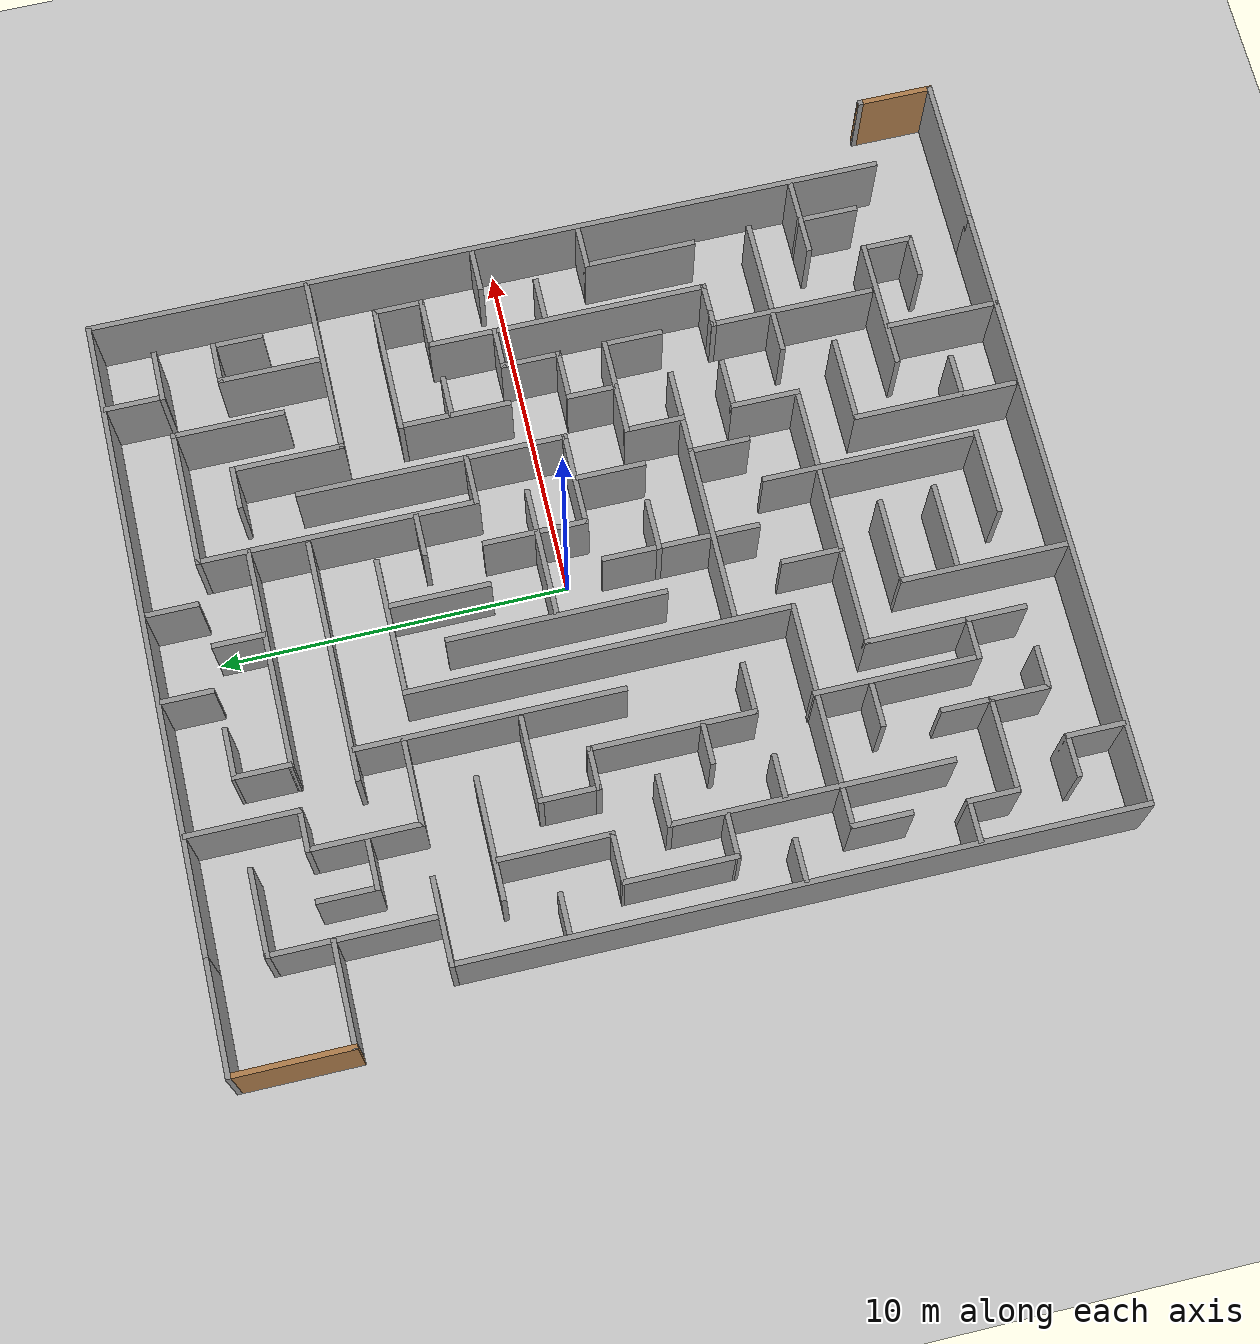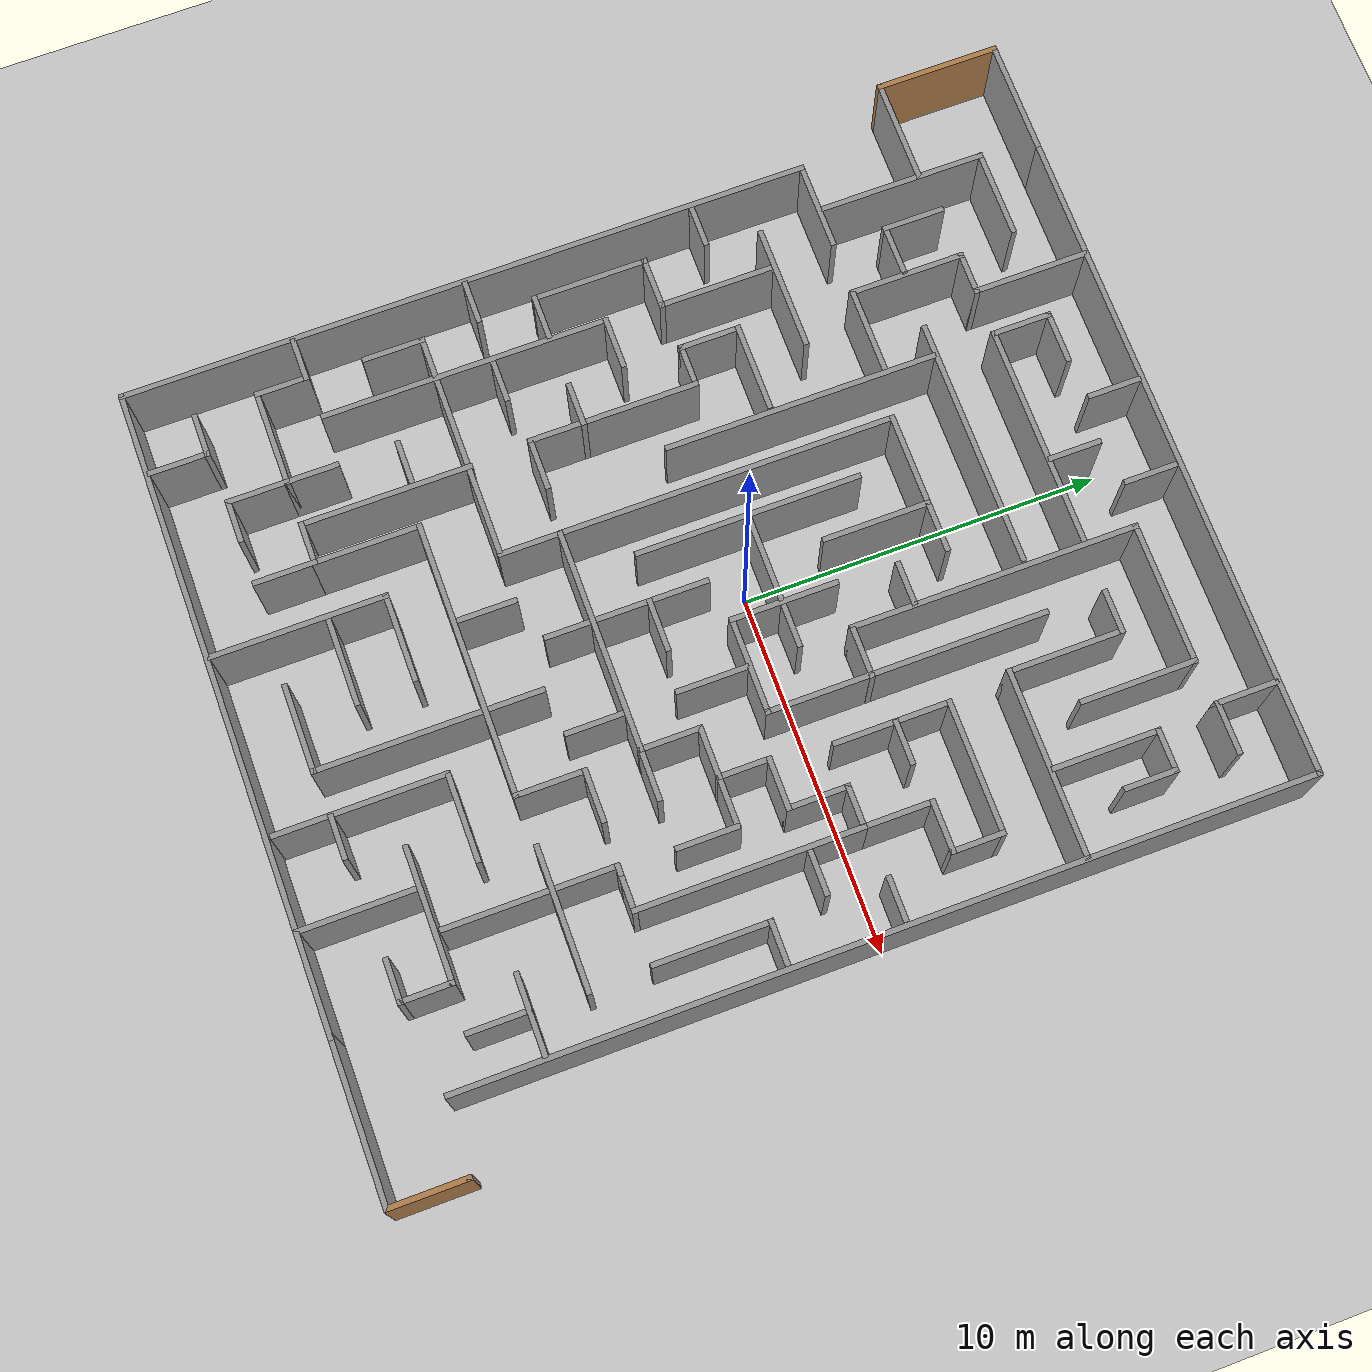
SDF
<sdf version="1.6">
 <world name="default">
  <plugin name="gazebo_occupancy_map" filename="libgazebo_grid_map_plugin.so">
   <map_resolution>0.05</map_resolution>
   <map_height>0.3</map_height>
   <map_size_x>30</map_size_x>
   <map_size_y>30</map_size_y>
   <init_robot_x>0</init_robot_x>
   <init_robot_y>0</init_robot_y>
  </plugin>
  <light name="sun" type="directional">
   <pose>0 0 10 0 -0 0</pose>
   <diffuse>0.8 0.8 0.8 1</diffuse>
   <specular>0.2 0.2 0.2 1</specular>
   <attenuation>
    <range>1000</range>
    <constant>0.9</constant>
    <linear>0.01</linear>
    <quadratic>0.001</quadratic>
   </attenuation>
   <direction>-0.5 0.1 -0.9</direction>
  </light>
  <model name="ground_plane">
   <static>1</static>
   <link name="link">
    <collision name="collision">
     <geometry><plane><normal>0 0 1</normal><size>100 100</size></plane></geometry>
     <surface><friction><ode><mu>100</mu><mu2>50</mu2></ode></friction></surface>
    </collision>
    <visual name="visual">
     <cast_shadows>0</cast_shadows>
     <geometry><plane><normal>0 0 1</normal><size>100 100</size></plane></geometry>
     <material>
      <script><uri>file://media/materials/scripts/gazebo.material</uri><name>Gazebo/Grey</name></script>
     </material>
    </visual>
   </link>
  </model>
  <gravity>0 0 -9.8</gravity>
  <magnetic_field>6e-06 2.3e-05 -4.2e-05</magnetic_field>
  <atmosphere type="adiabatic"/>
  <physics name="default_physics" default="0" type="ode">
   <max_step_size>0.001</max_step_size>
   <real_time_factor>1</real_time_factor>
   <real_time_update_rate>1000</real_time_update_rate>
  </physics>
  <scene><ambient>0.4 0.4 0.4 1</ambient><background>0.7 0.7 0.7 1</background><shadows>1</shadows></scene>
  <audio><device>default</device></audio>
  <spherical_coordinates>
   <surface_model>EARTH_WGS84</surface_model>
   <latitude_deg>0</latitude_deg>
   <longitude_deg>0</longitude_deg>
   <elevation>0</elevation>
   <heading_deg>0</heading_deg>
  </spherical_coordinates>
  <model name="maze">
   <pose>0.07616 -0.9851 0 0 -0 0</pose>
   <link name="Wall_10">
    <collision name="Wall_10_Collision">
     <geometry><box><size>18 0.15 2.5</size></box></geometry>
     <pose>0 0 1.25 0 -0 0</pose>
    </collision>
    <visual name="Wall_10_Visual">
     <pose>0 0 1.25 0 -0 0</pose>
     <geometry><box><size>18 0.15 2.5</size></box></geometry>
     <material>
      <script><uri>file://media/materials/scripts/gazebo.material</uri><name>Gazebo/Grey</name></script>
      <ambient>1 1 1 1</ambient>
     </material>
     <meta><layer>0</layer></meta>
    </visual>
    <pose>-1.40681 -12.6653 0 0 -0 0</pose>
   </link>
   <link name="Wall_100">
    <collision name="Wall_100_Collision">
     <geometry><box><size>1.5 0.15 2.5</size></box></geometry>
     <pose>0 0 1.25 0 -0 0</pose>
    </collision>
    <visual name="Wall_100_Visual">
     <pose>0 0 1.25 0 -0 0</pose>
     <geometry><box><size>1.5 0.15 2.5</size></box></geometry>
     <material>
      <script><uri>file://media/materials/scripts/gazebo.material</uri><name>Gazebo/Grey</name></script>
      <ambient>1 1 1 1</ambient>
     </material>
     <meta><layer>0</layer></meta>
    </visual>
    <pose>4.69711 -0.840511 0 0 -0 1.5708</pose>
   </link>
   <link name="Wall_101">
    <collision name="Wall_101_Collision">
     <geometry><box><size>1.5 0.15 2.5</size></box></geometry>
     <pose>0 0 1.25 0 -0 0</pose>
    </collision>
    <visual name="Wall_101_Visual">
     <pose>0 0 1.25 0 -0 0</pose>
     <geometry><box><size>1.5 0.15 2.5</size></box></geometry>
     <material>
      <script><uri>file://media/materials/scripts/gazebo.material</uri><name>Gazebo/Grey</name></script>
      <ambient>1 1 1 1</ambient>
     </material>
     <meta><layer>0</layer></meta>
    </visual>
    <pose>5.37211 -0.165511 0 0 -0 0</pose>
   </link>
   <link name="Wall_102">
    <collision name="Wall_102_Collision">
     <geometry><box><size>1.75 0.15 2.5</size></box></geometry>
     <pose>0 0 1.25 0 -0 0</pose>
    </collision>
    <visual name="Wall_102_Visual">
     <pose>0 0 1.25 0 -0 0</pose>
     <geometry><box><size>1.75 0.15 2.5</size></box></geometry>
     <material>
      <script><uri>file://media/materials/scripts/gazebo.material</uri><name>Gazebo/Grey</name></script>
      <ambient>1 1 1 1</ambient>
     </material>
     <meta><layer>0</layer></meta>
    </visual>
    <pose>6.04711 0.634489 0 0 -0 1.5708</pose>
   </link>
   <link name="Wall_103">
    <collision name="Wall_103_Collision">
     <geometry><box><size>1.25 0.15 2.5</size></box></geometry>
     <pose>0 0 1.25 0 -0 0</pose>
    </collision>
    <visual name="Wall_103_Visual">
     <pose>0 0 1.25 0 -0 0</pose>
     <geometry><box><size>1.25 0.15 2.5</size></box></geometry>
     <material>
      <script><uri>file://media/materials/scripts/gazebo.material</uri><name>Gazebo/Grey</name></script>
      <ambient>1 1 1 1</ambient>
     </material>
     <meta><layer>0</layer></meta>
    </visual>
    <pose>6.59711 1.43449 0 0 -0 0</pose>
   </link>
   <link name="Wall_104">
    <collision name="Wall_104_Collision">
     <geometry><box><size>6.25 0.15 2.5</size></box></geometry>
     <pose>0 0 1.25 0 -0 0</pose>
    </collision>
    <visual name="Wall_104_Visual">
     <pose>0 0 1.25 0 -0 0</pose>
     <geometry><box><size>6.25 0.15 2.5</size></box></geometry>
     <material>
      <script><uri>file://media/materials/scripts/gazebo.material</uri><name>Gazebo/Grey</name></script>
      <ambient>1 1 1 1</ambient>
     </material>
     <meta><layer>0</layer></meta>
    </visual>
    <pose>7.14711 -1.61551 0 0 -0 -1.5708</pose>
   </link>
   <link name="Wall_105">
    <collision name="Wall_105_Collision">
     <geometry><box><size>1 0.15 2.5</size></box></geometry>
     <pose>0 0 1.25 0 -0 0</pose>
    </collision>
    <visual name="Wall_105_Visual">
     <pose>0 0 1.25 0 -0 0</pose>
     <geometry><box><size>1 0.15 2.5</size></box></geometry>
     <material>
      <script><uri>file://media/materials/scripts/gazebo.material</uri><name>Gazebo/Grey</name></script>
      <ambient>1 1 1 1</ambient>
     </material>
     <meta><layer>0</layer></meta>
    </visual>
    <pose>6.72211 -4.66551 0 0 -0 3.14159</pose>
   </link>
   <link name="Wall_106">
    <collision name="Wall_106_Collision">
     <geometry><box><size>0.5 0.15 2.5</size></box></geometry>
     <pose>0 0 1.25 0 -0 0</pose>
    </collision>
    <visual name="Wall_106_Visual">
     <pose>0 0 1.25 0 -0 0</pose>
     <geometry><box><size>0.5 0.15 2.5</size></box></geometry>
     <material>
      <script><uri>file://media/materials/scripts/gazebo.material</uri><name>Gazebo/Grey</name></script>
      <ambient>1 1 1 1</ambient>
     </material>
     <meta><layer>0</layer></meta>
    </visual>
    <pose>6.12211 -4.66551 0 0 -0 3.14159</pose>
   </link>
   <link name="Wall_107">
    <collision name="Wall_107_Collision">
     <geometry><box><size>4.75 0.15 2.5</size></box></geometry>
     <pose>0 0 1.25 0 -0 0</pose>
    </collision>
    <visual name="Wall_107_Visual">
     <pose>0 0 1.25 0 -0 0</pose>
     <geometry><box><size>4.75 0.15 2.5</size></box></geometry>
     <material>
      <script><uri>file://media/materials/scripts/gazebo.material</uri><name>Gazebo/Grey</name></script>
      <ambient>1 1 1 1</ambient>
     </material>
     <meta><layer>0</layer></meta>
    </visual>
    <pose>5.94711 -6.96551 0 0 -0 -1.5708</pose>
   </link>
   <link name="Wall_109">
    <collision name="Wall_109_Collision">
     <geometry><box><size>4.5 0.15 2.5</size></box></geometry>
     <pose>0 0 1.25 0 -0 0</pose>
    </collision>
    <visual name="Wall_109_Visual">
     <pose>0 0 1.25 0 -0 0</pose>
     <geometry><box><size>4.5 0.15 2.5</size></box></geometry>
     <material>
      <script><uri>file://media/materials/scripts/gazebo.material</uri><name>Gazebo/Grey</name></script>
      <ambient>1 1 1 1</ambient>
     </material>
     <meta><layer>0</layer></meta>
    </visual>
    <pose>-0.252522 -2.20089 0 0 -0 -1.5708</pose>
   </link>
   <link name="Wall_111">
    <collision name="Wall_111_Collision">
     <geometry><box><size>1.5 0.15 2.5</size></box></geometry>
     <pose>0 0 1.25 0 -0 0</pose>
    </collision>
    <visual name="Wall_111_Visual">
     <pose>0 0 1.25 0 -0 0</pose>
     <geometry><box><size>1.5 0.15 2.5</size></box></geometry>
     <material>
      <script><uri>file://media/materials/scripts/gazebo.material</uri><name>Gazebo/Grey</name></script>
      <ambient>1 1 1 1</ambient>
     </material>
     <meta><layer>0</layer></meta>
    </visual>
    <pose>0.422478 -1.57708 0 0 -0 0</pose>
   </link>
   <link name="Wall_113">
    <collision name="Wall_113_Collision">
     <geometry><box><size>3 0.15 2.5</size></box></geometry>
     <pose>0 0 1.25 0 -0 0</pose>
    </collision>
    <visual name="Wall_113_Visual">
     <pose>0 0 1.25 0 -0 0</pose>
     <geometry><box><size>3 0.15 2.5</size></box></geometry>
     <material>
      <script><uri>file://media/materials/scripts/gazebo.material</uri><name>Gazebo/Grey</name></script>
      <ambient>1 1 1 1</ambient>
     </material>
     <meta><layer>0</layer></meta>
    </visual>
    <pose>-0.252522 4.66298 0 0 -0 -1.5708</pose>
   </link>
   <link name="Wall_115">
    <collision name="Wall_115_Collision">
     <geometry><box><size>6.25 0.15 2.5</size></box></geometry>
     <pose>0 0 1.25 0 -0 0</pose>
    </collision>
    <visual name="Wall_115_Visual">
     <pose>0 0 1.25 0 -0 0</pose>
     <geometry><box><size>6.25 0.15 2.5</size></box></geometry>
     <material>
      <script><uri>file://media/materials/scripts/gazebo.material</uri><name>Gazebo/Grey</name></script>
      <ambient>1 1 1 1</ambient>
     </material>
     <meta><layer>0</layer></meta>
    </visual>
    <pose>-1.56507 1.61746 0 0 -0 -1.5708</pose>
   </link>
   <link name="Wall_117">
    <collision name="Wall_117_Collision">
     <geometry><box><size>3.75 0.15 2.5</size></box></geometry>
     <pose>0 0 1.25 0 -0 0</pose>
    </collision>
    <visual name="Wall_117_Visual">
     <pose>0 0 1.25 0 -0 0</pose>
     <geometry><box><size>3.75 0.15 2.5</size></box></geometry>
     <material>
      <script><uri>file://media/materials/scripts/gazebo.material</uri><name>Gazebo/Grey</name></script>
      <ambient>1 1 1 1</ambient>
     </material>
     <meta><layer>0</layer></meta>
    </visual>
    <pose>0.354254 1.60485 0 0 -0 0</pose>
   </link>
   <link name="Wall_119">
    <collision name="Wall_119_Collision">
     <geometry><box><size>3 0.15 2.5</size></box></geometry>
     <pose>0 0 1.25 0 -0 0</pose>
    </collision>
    <visual name="Wall_119_Visual">
     <pose>0 0 1.25 0 -0 0</pose>
     <geometry><box><size>3 0.15 2.5</size></box></geometry>
     <material>
      <script><uri>file://media/materials/scripts/gazebo.material</uri><name>Gazebo/Grey</name></script>
      <ambient>1 1 1 1</ambient>
     </material>
     <meta><layer>0</layer></meta>
    </visual>
    <pose>0.940702 1.6515 0 0 -0 -1.5708</pose>
   </link>
   <link name="Wall_120">
    <collision name="Wall_120_Collision">
     <geometry><box><size>2.75 0.15 2.5</size></box></geometry>
     <pose>0 0 1.25 0 -0 0</pose>
    </collision>
    <visual name="Wall_120_Visual">
     <pose>0 0 1.25 0 -0 0</pose>
     <geometry><box><size>2.75 0.15 2.5</size></box></geometry>
     <material>
      <script><uri>file://media/materials/scripts/gazebo.material</uri><name>Gazebo/Grey</name></script>
      <ambient>1 1 1 1</ambient>
     </material>
     <meta><layer>0</layer></meta>
    </visual>
    <pose>2.2407 0.226497 0 0 -0 0</pose>
   </link>
   <link name="Wall_122">
    <collision name="Wall_122_Collision">
     <geometry><box><size>7.75 0.15 2.5</size></box></geometry>
     <pose>0 0 1.25 0 -0 0</pose>
    </collision>
    <visual name="Wall_122_Visual">
     <pose>0 0 1.25 0 -0 0</pose>
     <geometry><box><size>7.75 0.15 2.5</size></box></geometry>
     <material>
      <script><uri>file://media/materials/scripts/gazebo.material</uri><name>Gazebo/Grey</name></script>
      <ambient>1 1 1 1</ambient>
     </material>
     <meta><layer>0</layer></meta>
    </visual>
    <pose>3.5407 4.0265 0 0 -0 1.5708</pose>
   </link>
   <link name="Wall_124">
    <collision name="Wall_124_Collision">
     <geometry><box><size>2 0.15 2.5</size></box></geometry>
     <pose>0 0 1.25 0 -0 0</pose>
    </collision>
    <visual name="Wall_124_Visual">
     <pose>0 0 1.25 0 -0 0</pose>
     <geometry><box><size>2 0.15 2.5</size></box></geometry>
     <material>
      <script><uri>file://media/materials/scripts/gazebo.material</uri><name>Gazebo/Grey</name></script>
      <ambient>1 1 1 1</ambient>
     </material>
     <meta><layer>0</layer></meta>
    </visual>
    <pose>2.25325 -0.791789 0 0 -0 -1.5708</pose>
   </link>
   <link name="Wall_129">
    <collision name="Wall_129_Collision">
     <geometry><box><size>4.75 0.15 2.5</size></box></geometry>
     <pose>0 0 1.25 0 -0 0</pose>
    </collision>
    <visual name="Wall_129_Visual">
     <pose>0 0 1.25 0 -0 0</pose>
     <geometry><box><size>4.75 0.15 2.5</size></box></geometry>
     <material>
      <script><uri>file://media/materials/scripts/gazebo.material</uri><name>Gazebo/Grey</name></script>
      <ambient>1 1 1 1</ambient>
     </material>
     <meta><layer>0</layer></meta>
    </visual>
    <pose>2.25325 -10.1752 0 0 -0 1.5708</pose>
   </link>
   <link name="Wall_13">
    <collision name="Wall_13_Collision">
     <geometry><box><size>3.25 0.15 2.5</size></box></geometry>
     <pose>0 0 1.25 0 -0 0</pose>
    </collision>
    <visual name="Wall_13_Visual">
     <pose>0 0 1.25 0 -0 0</pose>
     <geometry><box><size>3.25 0.15 2.5</size></box></geometry>
     <material>
      <script><uri>file://media/materials/scripts/gazebo.material</uri><name>Gazebo/Grey</name></script>
      <ambient>1 1 1 1</ambient>
     </material>
     <meta><layer>0</layer></meta>
    </visual>
    <pose>-5.35339 11.0598 0 0 -0 -1.5708</pose>
   </link>
   <link name="Wall_130">
    <collision name="Wall_130_Collision">
     <geometry><box><size>2.5 0.15 2.5</size></box></geometry>
     <pose>0 0 1.25 0 -0 0</pose>
    </collision>
    <visual name="Wall_130_Visual">
     <pose>0 0 1.25 0 -0 0</pose>
     <geometry><box><size>2.5 0.15 2.5</size></box></geometry>
     <material>
      <script><uri>file://media/materials/scripts/gazebo.material</uri><name>Gazebo/Grey</name></script>
      <ambient>1 1 1 1</ambient>
     </material>
     <meta><layer>0</layer></meta>
    </visual>
    <pose>3.42825 -7.87519 0 0 -0 0</pose>
   </link>
   <link name="Wall_132">
    <collision name="Wall_132_Collision">
     <geometry><box><size>1.25 0.15 2.5</size></box></geometry>
     <pose>0 0 1.25 0 -0 0</pose>
    </collision>
    <visual name="Wall_132_Visual">
     <pose>0 0 1.25 0 -0 0</pose>
     <geometry><box><size>1.25 0.15 2.5</size></box></geometry>
     <material>
      <script><uri>file://media/materials/scripts/gazebo.material</uri><name>Gazebo/Grey</name></script>
      <ambient>1 1 1 1</ambient>
     </material>
     <meta><layer>0</layer></meta>
    </visual>
    <pose>2.84302 -10.9638 0 0 -0 0</pose>
   </link>
   <link name="Wall_134">
    <collision name="Wall_134_Collision">
     <geometry><box><size>3.75 0.15 2.5</size></box></geometry>
     <pose>0 0 1.25 0 -0 0</pose>
    </collision>
    <visual name="Wall_134_Visual">
     <pose>0 0 1.25 0 -0 0</pose>
     <geometry><box><size>3.75 0.15 2.5</size></box></geometry>
     <material>
      <script><uri>file://media/materials/scripts/gazebo.material</uri><name>Gazebo/Grey</name></script>
      <ambient>1 1 1 1</ambient>
     </material>
     <meta><layer>0</layer></meta>
    </visual>
    <pose>5.48512 -9.45236 0 0 -0 0</pose>
   </link>
   <link name="Wall_135">
    <collision name="Wall_135_Collision">
     <geometry><box><size>1.5 0.15 2.5</size></box></geometry>
     <pose>0 0 1.25 0 -0 0</pose>
    </collision>
    <visual name="Wall_135_Visual">
     <pose>0 0 1.25 0 -0 0</pose>
     <geometry><box><size>1.5 0.15 2.5</size></box></geometry>
     <material>
      <script><uri>file://media/materials/scripts/gazebo.material</uri><name>Gazebo/Grey</name></script>
      <ambient>1 1 1 1</ambient>
     </material>
     <meta><layer>0</layer></meta>
    </visual>
    <pose>7.28512 -10.1274 0 0 -0 -1.5708</pose>
   </link>
   <link name="Wall_136">
    <collision name="Wall_136_Collision">
     <geometry><box><size>1.25 0.15 2.5</size></box></geometry>
     <pose>0 0 1.25 0 -0 0</pose>
    </collision>
    <visual name="Wall_136_Visual">
     <pose>0 0 1.25 0 -0 0</pose>
     <geometry><box><size>1.25 0.15 2.5</size></box></geometry>
     <material>
      <script><uri>file://media/materials/scripts/gazebo.material</uri><name>Gazebo/Grey</name></script>
      <ambient>1 1 1 1</ambient>
     </material>
     <meta><layer>0</layer></meta>
    </visual>
    <pose>6.73512 -10.8024 0 0 -0 3.14159</pose>
   </link>
   <link name="Wall_138">
    <collision name="Wall_138_Collision">
     <geometry><box><size>3.25 0.15 2.5</size></box></geometry>
     <pose>0 0 1.25 0 -0 0</pose>
    </collision>
    <visual name="Wall_138_Visual">
     <pose>0 0 1.25 0 -0 0</pose>
     <geometry><box><size>3.25 0.15 2.5</size></box></geometry>
     <material>
      <script><uri>file://media/materials/scripts/gazebo.material</uri><name>Gazebo/Grey</name></script>
      <ambient>1 1 1 1</ambient>
     </material>
     <meta><layer>0</layer></meta>
    </visual>
    <pose>4.75902 -11.0819 0 0 -0 -1.5708</pose>
   </link>
   <link name="Wall_14">
    <collision name="Wall_14_Collision">
     <geometry><box><size>1.25 0.15 2.5</size></box></geometry>
     <pose>0 0 1.25 0 -0 0</pose>
    </collision>
    <visual name="Wall_14_Visual">
     <pose>0 0 1.25 0 -0 0</pose>
     <geometry><box><size>1.25 0.15 2.5</size></box></geometry>
     <material>
      <script><uri>file://media/materials/scripts/gazebo.material</uri><name>Gazebo/Grey</name></script>
      <ambient>1 1 1 1</ambient>
     </material>
     <meta><layer>0</layer></meta>
    </visual>
    <pose>-5.90339 9.5098 0 0 -0 3.14159</pose>
   </link>
   <link name="Wall_140">
    <collision name="Wall_140_Collision">
     <geometry><box><size>2.25 0.15 2.5</size></box></geometry>
     <pose>0 0 1.25 0 -0 0</pose>
    </collision>
    <visual name="Wall_140_Visual">
     <pose>0 0 1.25 0 -0 0</pose>
     <geometry><box><size>2.25 0.15 2.5</size></box></geometry>
     <material>
      <script><uri>file://media/materials/scripts/gazebo.material</uri><name>Gazebo/Grey</name></script>
      <ambient>1 1 1 1</ambient>
     </material>
     <meta><layer>0</layer></meta>
    </visual>
    <pose>8.68079 -7.90117 0 0 -0 3.14159</pose>
   </link>
   <link name="Wall_142">
    <collision name="Wall_142_Collision">
     <geometry><box><size>1.75 0.15 2.5</size></box></geometry>
     <pose>0 0 1.25 0 -0 0</pose>
    </collision>
    <visual name="Wall_142_Visual">
     <pose>0 0 1.25 0 -0 0</pose>
     <geometry><box><size>1.75 0.15 2.5</size></box></geometry>
     <material>
      <script><uri>file://media/materials/scripts/gazebo.material</uri><name>Gazebo/Grey</name></script>
      <ambient>1 1 1 1</ambient>
     </material>
     <meta><layer>0</layer></meta>
    </visual>
    <pose>8.57734 -8.70116 0 0 -0 -1.5708</pose>
   </link>
   <link name="Wall_144">
    <collision name="Wall_144_Collision">
     <geometry><box><size>4 0.15 2.5</size></box></geometry>
     <pose>0 0 1.25 0 -0 0</pose>
    </collision>
    <visual name="Wall_144_Visual">
     <pose>0 0 1.25 0 -0 0</pose>
     <geometry><box><size>4 0.15 2.5</size></box></geometry>
     <material>
      <script><uri>file://media/materials/scripts/gazebo.material</uri><name>Gazebo/Grey</name></script>
      <ambient>1 1 1 1</ambient>
     </material>
     <meta><layer>0</layer></meta>
    </visual>
    <pose>6.72379 -6.38975 0 0 -0 0</pose>
   </link>
   <link name="Wall_146">
    <collision name="Wall_146_Collision">
     <geometry><box><size>3.25 0.15 2.5</size></box></geometry>
     <pose>0 0 1.25 0 -0 0</pose>
    </collision>
    <visual name="Wall_146_Visual">
     <pose>0 0 1.25 0 -0 0</pose>
     <geometry><box><size>3.25 0.15 2.5</size></box></geometry>
     <material>
      <script><uri>file://media/materials/scripts/gazebo.material</uri><name>Gazebo/Grey</name></script>
      <ambient>1 1 1 1</ambient>
     </material>
     <meta><layer>0</layer></meta>
    </visual>
    <pose>8.57734 -3.12946 0 0 -0 1.5708</pose>
   </link>
   <link name="Wall_147">
    <collision name="Wall_147_Collision">
     <geometry><box><size>1.25 0.15 2.5</size></box></geometry>
     <pose>0 0 1.25 0 -0 0</pose>
    </collision>
    <visual name="Wall_147_Visual">
     <pose>0 0 1.25 0 -0 0</pose>
     <geometry><box><size>1.25 0.15 2.5</size></box></geometry>
     <material>
      <script><uri>file://media/materials/scripts/gazebo.material</uri><name>Gazebo/Grey</name></script>
      <ambient>1 1 1 1</ambient>
     </material>
     <meta><layer>0</layer></meta>
    </visual>
    <pose>9.12734 -1.57946 0 0 -0 0</pose>
   </link>
   <link name="Wall_149">
    <collision name="Wall_149_Collision">
     <geometry><box><size>2 0.15 2.5</size></box></geometry>
     <pose>0 0 1.25 0 -0 0</pose>
    </collision>
    <visual name="Wall_149_Visual">
     <pose>0 0 1.25 0 -0 0</pose>
     <geometry><box><size>2 0.15 2.5</size></box></geometry>
     <material>
      <script><uri>file://media/materials/scripts/gazebo.material</uri><name>Gazebo/Grey</name></script>
      <ambient>1 1 1 1</ambient>
     </material>
     <meta><layer>0</layer></meta>
    </visual>
    <pose>7.14711 2.35949 0 0 -0 1.5708</pose>
   </link>
   <link name="Wall_15">
    <collision name="Wall_15_Collision">
     <geometry><box><size>3.25 0.15 2.5</size></box></geometry>
     <pose>0 0 1.25 0 -0 0</pose>
    </collision>
    <visual name="Wall_15_Visual">
     <pose>0 0 1.25 0 -0 0</pose>
     <geometry><box><size>3.25 0.15 2.5</size></box></geometry>
     <material>
      <script><uri>file://media/materials/scripts/gazebo.material</uri><name>Gazebo/Grey</name></script>
      <ambient>1 1 1 1</ambient>
     </material>
     <meta><layer>0</layer></meta>
    </visual>
    <pose>-6.45339 7.9598 0 0 -0 -1.5708</pose>
   </link>
   <link name="Wall_150">
    <collision name="Wall_150_Collision">
     <geometry><box><size>1.5 0.15 2.5</size></box></geometry>
     <pose>0 0 1.25 0 -0 0</pose>
    </collision>
    <visual name="Wall_150_Visual">
     <pose>0 0 1.25 0 -0 0</pose>
     <geometry><box><size>1.5 0.15 2.5</size></box></geometry>
     <material>
      <script><uri>file://media/materials/scripts/gazebo.material</uri><name>Gazebo/Grey</name></script>
      <ambient>1 1 1 1</ambient>
     </material>
     <meta><layer>0</layer></meta>
    </visual>
    <pose>7.82211 3.28449 0 0 -0 0</pose>
   </link>
   <link name="Wall_151">
    <collision name="Wall_151_Collision">
     <geometry><box><size>1.5 0.15 2.5</size></box></geometry>
     <pose>0 0 1.25 0 -0 0</pose>
    </collision>
    <visual name="Wall_151_Visual">
     <pose>0 0 1.25 0 -0 0</pose>
     <geometry><box><size>1.5 0.15 2.5</size></box></geometry>
     <material>
      <script><uri>file://media/materials/scripts/gazebo.material</uri><name>Gazebo/Grey</name></script>
      <ambient>1 1 1 1</ambient>
     </material>
     <meta><layer>0</layer></meta>
    </visual>
    <pose>8.49711 3.95949 0 0 -0 1.5708</pose>
   </link>
   <link name="Wall_152">
    <collision name="Wall_152_Collision">
     <geometry><box><size>3.75 0.15 2.5</size></box></geometry>
     <pose>0 0 1.25 0 -0 0</pose>
    </collision>
    <visual name="Wall_152_Visual">
     <pose>0 0 1.25 0 -0 0</pose>
     <geometry><box><size>3.75 0.15 2.5</size></box></geometry>
     <material>
      <script><uri>file://media/materials/scripts/gazebo.material</uri><name>Gazebo/Grey</name></script>
      <ambient>1 1 1 1</ambient>
     </material>
     <meta><layer>0</layer></meta>
    </visual>
    <pose>6.69711 4.63449 0 0 -0 3.14159</pose>
   </link>
   <link name="Wall_153">
    <collision name="Wall_153_Collision">
     <geometry><box><size>3.25 0.15 2.5</size></box></geometry>
     <pose>0 0 1.25 0 -0 0</pose>
    </collision>
    <visual name="Wall_153_Visual">
     <pose>0 0 1.25 0 -0 0</pose>
     <geometry><box><size>3.25 0.15 2.5</size></box></geometry>
     <material>
      <script><uri>file://media/materials/scripts/gazebo.material</uri><name>Gazebo/Grey</name></script>
      <ambient>1 1 1 1</ambient>
     </material>
     <meta><layer>0</layer></meta>
    </visual>
    <pose>4.89711 3.08449 0 0 -0 -1.5708</pose>
   </link>
   <link name="Wall_155">
    <collision name="Wall_155_Collision">
     <geometry><box><size>1.25 0.15 2.5</size></box></geometry>
     <pose>0 0 1.25 0 -0 0</pose>
    </collision>
    <visual name="Wall_155_Visual">
     <pose>0 0 1.25 0 -0 0</pose>
     <geometry><box><size>1.25 0.15 2.5</size></box></geometry>
     <material>
      <script><uri>file://media/materials/scripts/gazebo.material</uri><name>Gazebo/Grey</name></script>
      <ambient>1 1 1 1</ambient>
     </material>
     <meta><layer>0</layer></meta>
    </visual>
    <pose>5.47255 3.17028 0 0 -0 0</pose>
   </link>
   <link name="Wall_157">
    <collision name="Wall_157_Collision">
     <geometry><box><size>1.25 0.15 2.5</size></box></geometry>
     <pose>0 0 1.25 0 -0 0</pose>
    </collision>
    <visual name="Wall_157_Visual">
     <pose>0 0 1.25 0 -0 0</pose>
     <geometry><box><size>1.25 0.15 2.5</size></box></geometry>
     <material>
      <script><uri>file://media/materials/scripts/gazebo.material</uri><name>Gazebo/Grey</name></script>
      <ambient>1 1 1 1</ambient>
     </material>
     <meta><layer>0</layer></meta>
    </visual>
    <pose>4.12369 9.46497 0 0 -0 0</pose>
   </link>
   <link name="Wall_158">
    <collision name="Wall_158_Collision">
     <geometry><box><size>3.25 0.15 2.5</size></box></geometry>
     <pose>0 0 1.25 0 -0 0</pose>
    </collision>
    <visual name="Wall_158_Visual">
     <pose>0 0 1.25 0 -0 0</pose>
     <geometry><box><size>3.25 0.15 2.5</size></box></geometry>
     <material>
      <script><uri>file://media/materials/scripts/gazebo.material</uri><name>Gazebo/Grey</name></script>
      <ambient>1 1 1 1</ambient>
     </material>
     <meta><layer>0</layer></meta>
    </visual>
    <pose>4.67369 7.91497 0 0 -0 -1.5708</pose>
   </link>
   <link name="Wall_159">
    <collision name="Wall_159_Collision">
     <geometry><box><size>5.25 0.15 2.5</size></box></geometry>
     <pose>0 0 1.25 0 -0 0</pose>
    </collision>
    <visual name="Wall_159_Visual">
     <pose>0 0 1.25 0 -0 0</pose>
     <geometry><box><size>5.25 0.15 2.5</size></box></geometry>
     <material>
      <script><uri>file://media/materials/scripts/gazebo.material</uri><name>Gazebo/Grey</name></script>
      <ambient>1 1 1 1</ambient>
     </material>
     <meta><layer>0</layer></meta>
    </visual>
    <pose>7.22369 6.36497 0 0 -0 0</pose>
   </link>
   <link name="Wall_16">
    <collision name="Wall_16_Collision">
     <geometry><box><size>2.5 0.15 2.5</size></box></geometry>
     <pose>0 0 1.25 0 -0 0</pose>
    </collision>
    <visual name="Wall_16_Visual">
     <pose>0 0 1.25 0 -0 0</pose>
     <geometry><box><size>2.5 0.15 2.5</size></box></geometry>
     <material>
      <script><uri>file://media/materials/scripts/gazebo.material</uri><name>Gazebo/Grey</name></script>
      <ambient>1 1 1 1</ambient>
     </material>
     <meta><layer>0</layer></meta>
    </visual>
    <pose>-5.27839 6.4098 0 0 -0 0</pose>
   </link>
   <link name="Wall_161">
    <collision name="Wall_161_Collision">
     <geometry><box><size>3 0.15 2.5</size></box></geometry>
     <pose>0 0 1.25 0 -0 0</pose>
    </collision>
    <visual name="Wall_161_Visual">
     <pose>0 0 1.25 0 -0 0</pose>
     <geometry><box><size>3 0.15 2.5</size></box></geometry>
     <material>
      <script><uri>file://media/materials/scripts/gazebo.material</uri><name>Gazebo/Grey</name></script>
      <ambient>1 1 1 1</ambient>
     </material>
     <meta><layer>0</layer></meta>
    </visual>
    <pose>7.41276 7.88097 0 0 -0 1.5708</pose>
   </link>
   <link name="Wall_162">
    <collision name="Wall_162_Collision">
     <geometry><box><size>1.25 0.15 2.5</size></box></geometry>
     <pose>0 0 1.25 0 -0 0</pose>
    </collision>
    <visual name="Wall_162_Visual">
     <pose>0 0 1.25 0 -0 0</pose>
     <geometry><box><size>1.25 0.15 2.5</size></box></geometry>
     <material>
      <script><uri>file://media/materials/scripts/gazebo.material</uri><name>Gazebo/Grey</name></script>
      <ambient>1 1 1 1</ambient>
     </material>
     <meta><layer>0</layer></meta>
    </visual>
    <pose>7.96276 9.30597 0 0 -0 0</pose>
   </link>
   <link name="Wall_163">
    <collision name="Wall_163_Collision">
     <geometry><box><size>1.5 0.15 2.5</size></box></geometry>
     <pose>0 0 1.25 0 -0 0</pose>
    </collision>
    <visual name="Wall_163_Visual">
     <pose>0 0 1.25 0 -0 0</pose>
     <geometry><box><size>1.5 0.15 2.5</size></box></geometry>
     <material>
      <script><uri>file://media/materials/scripts/gazebo.material</uri><name>Gazebo/Grey</name></script>
      <ambient>1 1 1 1</ambient>
     </material>
     <meta><layer>0</layer></meta>
    </visual>
    <pose>8.51276 8.63097 0 0 -0 -1.5708</pose>
   </link>
   <link name="Wall_167">
    <collision name="Wall_167_Collision">
     <geometry><box><size>1.5 0.15 2.5</size></box></geometry>
     <pose>0 0 1.25 0 -0 0</pose>
    </collision>
    <visual name="Wall_167_Visual">
     <pose>0 0 1.25 0 -0 0</pose>
     <geometry><box><size>1.5 0.15 2.5</size></box></geometry>
     <material>
      <script><uri>file://media/materials/scripts/gazebo.material</uri><name>Gazebo/Grey</name></script>
      <ambient>1 1 1 1</ambient>
     </material>
     <meta><layer>0</layer></meta>
    </visual>
    <pose>7.94942 10.9894 0 0 -0 0</pose>
   </link>
   <link name="Wall_169">
    <collision name="Wall_169_Collision">
     <geometry><box><size>1.75 0.15 2.5</size></box></geometry>
     <pose>0 0 1.25 0 -0 0</pose>
    </collision>
    <visual name="Wall_169_Visual">
     <pose>0 0 1.25 0 -0 0</pose>
     <geometry><box><size>1.75 0.15 2.5</size></box></geometry>
     <material>
      <script><uri>file://media/materials/scripts/gazebo.material</uri><name>Gazebo/Grey</name></script>
      <ambient>1 1 1 1</ambient>
     </material>
     <meta><layer>0</layer></meta>
    </visual>
    <pose>7.27442 11.7894 0 0 -0 1.5708</pose>
   </link>
   <link name="Wall_171">
    <collision name="Wall_171_Collision">
     <geometry><box><size>1.5 0.15 2.5</size></box></geometry>
     <pose>0 0 1.25 0 -0 0</pose>
    </collision>
    <visual name="Wall_171_Visual">
     <pose>0 0 1.25 0 -0 0</pose>
     <geometry><box><size>1.5 0.15 2.5</size></box></geometry>
     <material>
      <script><uri>file://media/materials/scripts/gazebo.material</uri><name>Gazebo/Grey</name></script>
      <ambient>1 1 1 1</ambient>
     </material>
     <meta><layer>0</layer></meta>
    </visual>
    <pose>0.993011 11.8294 0 0 -0 -1.5708</pose>
   </link>
   <link name="Wall_173">
    <collision name="Wall_173_Collision">
     <geometry><box><size>1.25 0.15 2.5</size></box></geometry>
     <pose>0 0 1.25 0 -0 0</pose>
    </collision>
    <visual name="Wall_173_Visual">
     <pose>0 0 1.25 0 -0 0</pose>
     <geometry><box><size>1.25 0.15 2.5</size></box></geometry>
     <material>
      <script><uri>file://media/materials/scripts/gazebo.material</uri><name>Gazebo/Grey</name></script>
      <ambient>1 1 1 1</ambient>
     </material>
     <meta><layer>0</layer></meta>
    </visual>
    <pose>1.58262 4.76575 0 0 -0 0</pose>
   </link>
   <link name="Wall_175">
    <collision name="Wall_175_Collision">
     <geometry><box><size>1.5 0.15 2.5</size></box></geometry>
     <pose>0 0 1.25 0 -0 0</pose>
    </collision>
    <visual name="Wall_175_Visual">
     <pose>0 0 1.25 0 -0 0</pose>
     <geometry><box><size>1.5 0.15 2.5</size></box></geometry>
     <material>
      <script><uri>file://media/materials/scripts/gazebo.material</uri><name>Gazebo/Grey</name></script>
      <ambient>1 1 1 1</ambient>
     </material>
     <meta><layer>0</layer></meta>
    </visual>
    <pose>5.37211 -1.51551 0 0 -0 0</pose>
   </link>
   <link name="Wall_176">
    <collision name="Wall_176_Collision">
     <geometry><box><size>1.75 0.15 2.5</size></box></geometry>
     <pose>0 0 1.25 0 -0 0</pose>
    </collision>
    <visual name="Wall_176_Visual">
     <pose>0 0 1.25 0 -0 0</pose>
     <geometry><box><size>1.75 0.15 2.5</size></box></geometry>
     <material>
      <script><uri>file://media/materials/scripts/gazebo.material</uri><name>Gazebo/Grey</name></script>
      <ambient>1 1 1 1</ambient>
     </material>
     <meta><layer>0</layer></meta>
    </visual>
    <pose>6.04711 -2.31551 0 0 -0 -1.5708</pose>
   </link>
   <link name="Wall_178">
    <collision name="Wall_178_Collision">
     <geometry><box><size>1.25 0.15 2.5</size></box></geometry>
     <pose>0 0 1.25 0 -0 0</pose>
    </collision>
    <visual name="Wall_178_Visual">
     <pose>0 0 1.25 0 -0 0</pose>
     <geometry><box><size>1.25 0.15 2.5</size></box></geometry>
     <material>
      <script><uri>file://media/materials/scripts/gazebo.material</uri><name>Gazebo/Grey</name></script>
      <ambient>1 1 1 1</ambient>
     </material>
     <meta><layer>0</layer></meta>
    </visual>
    <pose>9.12241 1.54923 0 0 -0 0</pose>
   </link>
   <link name="Wall_18">
    <collision name="Wall_18_Collision">
     <geometry><box><size>1.75 0.15 2.5</size></box></geometry>
     <pose>0 0 1.25 0 -0 0</pose>
    </collision>
    <visual name="Wall_18_Visual">
     <pose>0 0 1.25 0 -0 0</pose>
     <geometry><box><size>1.75 0.15 2.5</size></box></geometry>
     <material>
      <script><uri>file://media/materials/scripts/gazebo.material</uri><name>Gazebo/Grey</name></script>
      <ambient>1 1 1 1</ambient>
     </material>
     <meta><layer>0</layer></meta>
    </visual>
    <pose>-7.88456 8.70516 0 0 -0 -1.5708</pose>
   </link>
   <link name="Wall_180">
    <collision name="Wall_180_Collision">
     <geometry><box><size>1.25 0.15 2.5</size></box></geometry>
     <pose>0 0 1.25 0 -0 0</pose>
    </collision>
    <visual name="Wall_180_Visual">
     <pose>0 0 1.25 0 -0 0</pose>
     <geometry><box><size>1.25 0.15 2.5</size></box></geometry>
     <material>
      <script><uri>file://media/materials/scripts/gazebo.material</uri><name>Gazebo/Grey</name></script>
      <ambient>1 1 1 1</ambient>
     </material>
     <meta><layer>0</layer></meta>
    </visual>
    <pose>7.84272 -0.041733 0 0 -0 0</pose>
   </link>
   <link name="Wall_182">
    <collision name="Wall_182_Collision">
     <geometry><box><size>1.5 0.15 2.5</size></box></geometry>
     <pose>0 0 1.25 0 -0 0</pose>
    </collision>
    <visual name="Wall_182_Visual">
     <pose>0 0 1.25 0 -0 0</pose>
     <geometry><box><size>1.5 0.15 2.5</size></box></geometry>
     <material>
      <script><uri>file://media/materials/scripts/gazebo.material</uri><name>Gazebo/Grey</name></script>
      <ambient>1 1 1 1</ambient>
     </material>
     <meta><layer>0</layer></meta>
    </visual>
    <pose>4.02211 -3.11551 0 0 -0 0</pose>
   </link>
   <link name="Wall_184">
    <collision name="Wall_184_Collision">
     <geometry><box><size>1.25 0.15 2.5</size></box></geometry>
     <pose>0 0 1.25 0 -0 0</pose>
    </collision>
    <visual name="Wall_184_Visual">
     <pose>0 0 1.25 0 -0 0</pose>
     <geometry><box><size>1.25 0.15 2.5</size></box></geometry>
     <material>
      <script><uri>file://media/materials/scripts/gazebo.material</uri><name>Gazebo/Grey</name></script>
      <ambient>1 1 1 1</ambient>
     </material>
     <meta><layer>0</layer></meta>
    </visual>
    <pose>-6.02635 -6.26725 0 0 -0 0</pose>
   </link>
   <link name="Wall_187">
    <collision name="Wall_187_Collision">
     <geometry><box><size>3.25 0.15 2.5</size></box></geometry>
     <pose>0 0 1.25 0 -0 0</pose>
    </collision>
    <visual name="Wall_187_Visual">
     <pose>0 0 1.25 0 -0 0</pose>
     <geometry><box><size>3.25 0.15 2.5</size></box></geometry>
     <material>
      <script><uri>file://media/materials/scripts/gazebo.material</uri><name>Gazebo/Grey</name></script>
      <ambient>1 1 1 1</ambient>
     </material>
     <meta><layer>0</layer></meta>
    </visual>
    <pose>-10.3182 12.6653 0 0 -0 3.14159</pose>
   </link>
   <link name="Wall_188">
    <collision name="Wall_188_Collision">
     <geometry><box><size>3.5 0.15 2.5</size></box></geometry>
     <pose>0 0 1.25 0 -0 0</pose>
    </collision>
    <visual name="Wall_188_Visual">
     <pose>0 0 1.25 0 -0 0</pose>
     <geometry><box><size>3.5 0.15 2.5</size></box></geometry>
     <material>
      <script><uri>file://media/materials/scripts/gazebo.material</uri><name>Gazebo/Wood</name></script>
      <ambient>1 1 1 1</ambient>
     </material>
     <meta><layer>0</layer></meta>
    </visual>
    <pose>-11.8682 10.9903 0 0 -0 -1.5708</pose>
   </link>
   <link name="Wall_189">
    <collision name="Wall_189_Collision">
     <geometry><box><size>3 0.15 2.5</size></box></geometry>
     <pose>0 0 1.25 0 -0 0</pose>
    </collision>
    <visual name="Wall_189_Visual">
     <pose>0 0 1.25 0 -0 0</pose>
     <geometry><box><size>3 0.15 2.5</size></box></geometry>
     <material>
      <script><uri>file://media/materials/scripts/gazebo.material</uri><name>Gazebo/Grey</name></script>
      <ambient>1 1 1 1</ambient>
     </material>
     <meta><layer>0</layer></meta>
    </visual>
    <pose>-10.4432 9.31531 0 0 -0 0</pose>
   </link>
   <link name="Wall_19">
    <collision name="Wall_19_Collision">
     <geometry><box><size>1.5 0.15 2.5</size></box></geometry>
     <pose>0 0 1.25 0 -0 0</pose>
    </collision>
    <visual name="Wall_19_Visual">
     <pose>0 0 1.25 0 -0 0</pose>
     <geometry><box><size>1.5 0.15 2.5</size></box></geometry>
     <material>
      <script><uri>file://media/materials/scripts/gazebo.material</uri><name>Gazebo/Grey</name></script>
      <ambient>1 1 1 1</ambient>
     </material>
     <meta><layer>0</layer></meta>
    </visual>
    <pose>-7.20956 7.90516 0 0 -0 0</pose>
   </link>
   <link name="Wall_192">
    <collision name="Wall_192_Collision">
     <geometry><box><size>1.75 0.15 2.5</size></box></geometry>
     <pose>0 0 1.25 0 -0 0</pose>
    </collision>
    <visual name="Wall_192_Visual">
     <pose>0 0 1.25 0 -0 0</pose>
     <geometry><box><size>1.75 0.15 2.5</size></box></geometry>
     <material>
      <script><uri>file://media/materials/scripts/gazebo.material</uri><name>Gazebo/Grey</name></script>
      <ambient>1 1 1 1</ambient>
     </material>
     <meta><layer>0</layer></meta>
    </visual>
    <pose>2.311 -3.92815 0 0 -0 -1.5708</pose>
   </link>
   <link name="Wall_195">
    <collision name="Wall_195_Collision">
     <geometry><box><size>4.5 0.15 2.5</size></box></geometry>
     <pose>0 0 1.25 0 -0 0</pose>
    </collision>
    <visual name="Wall_195_Visual">
     <pose>0 0 1.25 0 -0 0</pose>
     <geometry><box><size>4.5 0.15 2.5</size></box></geometry>
     <material>
      <script><uri>file://media/materials/scripts/gazebo.material</uri><name>Gazebo/Grey</name></script>
      <ambient>1 1 1 1</ambient>
     </material>
     <meta><layer>0</layer></meta>
    </visual>
    <pose>9.69319 -12.6653 0 0 -0 0</pose>
   </link>
   <link name="Wall_197">
    <collision name="Wall_197_Collision">
     <geometry><box><size>0.15 0.15 2.5</size></box></geometry>
     <pose>0 0 1.25 0 -0 0</pose>
    </collision>
    <visual name="Wall_197_Visual">
     <pose>0 0 1.25 0 -0 0</pose>
     <geometry><box><size>0.15 0.15 2.5</size></box></geometry>
     <material>
      <script><uri>file://media/materials/scripts/gazebo.material</uri><name>Gazebo/Grey</name></script>
      <ambient>1 1 1 1</ambient>
     </material>
     <meta><layer>0</layer></meta>
    </visual>
    <pose>11.8682 -10.5653 0 0 -0 0</pose>
   </link>
   <link name="Wall_2">
    <collision name="Wall_2_Collision">
     <geometry><box><size>18.75 0.15 2.5</size></box></geometry>
     <pose>0 0 1.25 0 -0 0</pose>
    </collision>
    <visual name="Wall_2_Visual">
     <pose>0 0 1.25 0 -0 0</pose>
     <geometry><box><size>18.75 0.15 2.5</size></box></geometry>
     <material>
      <script><uri>file://media/materials/scripts/gazebo.material</uri><name>Gazebo/Grey</name></script>
      <ambient>1 1 1 1</ambient>
     </material>
     <meta><layer>0</layer></meta>
    </visual>
    <pose>0.531805 12.6653 0 0 -0 0</pose>
   </link>
   <link name="Wall_201">
    <collision name="Wall_201_Collision">
     <geometry><box><size>2.25 0.15 2.5</size></box></geometry>
     <pose>0 0 1.25 0 -0 0</pose>
    </collision>
    <visual name="Wall_201_Visual">
     <pose>0 0 1.25 0 -0 0</pose>
     <geometry><box><size>2.25 0.15 2.5</size></box></geometry>
     <material>
      <script><uri>file://media/materials/scripts/gazebo.material</uri><name>Gazebo/Wood</name></script>
      <ambient>1 1 1 1</ambient>
     </material>
     <meta><layer>0</layer></meta>
    </visual>
    <pose>11.8682 -11.6153 0 0 -0 -1.5708</pose>
   </link>
   <link name="Wall_21">
    <collision name="Wall_21_Collision">
     <geometry><box><size>1.5 0.15 2.5</size></box></geometry>
     <pose>0 0 1.25 0 -0 0</pose>
    </collision>
    <visual name="Wall_21_Visual">
     <pose>0 0 1.25 0 -0 0</pose>
     <geometry><box><size>1.5 0.15 2.5</size></box></geometry>
     <material>
      <script><uri>file://media/materials/scripts/gazebo.material</uri><name>Gazebo/Grey</name></script>
      <ambient>1 1 1 1</ambient>
     </material>
     <meta><layer>0</layer></meta>
    </visual>
    <pose>-1.54038 11.8707 0 0 -0 -1.5708</pose>
   </link>
   <link name="Wall_23">
    <collision name="Wall_23_Collision">
     <geometry><box><size>1.5 0.15 2.5</size></box></geometry>
     <pose>0 0 1.25 0 -0 0</pose>
    </collision>
    <visual name="Wall_23_Visual">
     <pose>0 0 1.25 0 -0 0</pose>
     <geometry><box><size>1.5 0.15 2.5</size></box></geometry>
     <material>
      <script><uri>file://media/materials/scripts/gazebo.material</uri><name>Gazebo/Grey</name></script>
      <ambient>1 1 1 1</ambient>
     </material>
     <meta><layer>0</layer></meta>
    </visual>
    <pose>-3.38072 11.0448 0 0 -0 3.14159</pose>
   </link>
   <link name="Wall_24">
    <collision name="Wall_24_Collision">
     <geometry><box><size>1.65825 0.15 2.5</size></box></geometry>
     <pose>0 0 1.25 0 -0 0</pose>
    </collision>
    <visual name="Wall_24_Visual">
     <pose>0 0 1.25 0 -0 0</pose>
     <geometry><box><size>1.65825 0.15 2.5</size></box></geometry>
     <material>
      <script><uri>file://media/materials/scripts/gazebo.material</uri><name>Gazebo/Grey</name></script>
      <ambient>1 1 1 1</ambient>
     </material>
     <meta><layer>0</layer></meta>
    </visual>
    <pose>-4.05594 10.2907 0 0 -0 -1.57109</pose>
   </link>
   <link name="Wall_25">
    <collision name="Wall_25_Collision">
     <geometry><box><size>6.36 0.15 2.5</size></box></geometry>
     <pose>0 0 1.25 0 -0 0</pose>
    </collision>
    <visual name="Wall_25_Visual">
     <pose>0 0 1.25 0 -0 0</pose>
     <geometry><box><size>6.36 0.15 2.5</size></box></geometry>
     <material>
      <script><uri>file://media/materials/scripts/gazebo.material</uri><name>Gazebo/Grey</name></script>
      <ambient>1 1 1 1</ambient>
     </material>
     <meta><layer>0</layer></meta>
    </visual>
    <pose>-0.951161 9.49081 0 0 -0 0</pose>
   </link>
   <link name="Wall_27">
    <collision name="Wall_27_Collision">
     <geometry><box><size>1.5 0.15 2.5</size></box></geometry>
     <pose>0 0 1.25 0 -0 0</pose>
    </collision>
    <visual name="Wall_27_Visual">
     <pose>0 0 1.25 0 -0 0</pose>
     <geometry><box><size>1.5 0.15 2.5</size></box></geometry>
     <material>
      <script><uri>file://media/materials/scripts/gazebo.material</uri><name>Gazebo/Grey</name></script>
      <ambient>1 1 1 1</ambient>
     </material>
     <meta><layer>0</layer></meta>
    </visual>
    <pose>-0.284084 10.2206 0 0 -0 -1.5708</pose>
   </link>
   <link name="Wall_29">
    <collision name="Wall_29_Collision">
     <geometry><box><size>3.25 0.15 2.5</size></box></geometry>
     <pose>0 0 1.25 0 -0 0</pose>
    </collision>
    <visual name="Wall_29_Visual">
     <pose>0 0 1.25 0 -0 0</pose>
     <geometry><box><size>3.25 0.15 2.5</size></box></geometry>
     <material>
      <script><uri>file://media/materials/scripts/gazebo.material</uri><name>Gazebo/Grey</name></script>
      <ambient>1 1 1 1</ambient>
     </material>
     <meta><layer>0</layer></meta>
    </visual>
    <pose>6.04956 9.34284 0 0 -0 1.5708</pose>
   </link>
   <link name="Wall_3">
    <collision name="Wall_3_Collision">
     <geometry><box><size>23.25 0.15 2.5</size></box></geometry>
     <pose>0 0 1.25 0 -0 0</pose>
    </collision>
    <visual name="Wall_3_Visual">
     <pose>0 0 1.25 0 -0 0</pose>
     <geometry><box><size>23.25 0.15 2.5</size></box></geometry>
     <material>
      <script><uri>file://media/materials/scripts/gazebo.material</uri><name>Gazebo/Grey</name></script>
      <ambient>1 1 1 1</ambient>
     </material>
     <meta><layer>0</layer></meta>
    </visual>
    <pose>9.8318 1.11531 0 0 -0 -1.5708</pose>
   </link>
   <link name="Wall_30">
    <collision name="Wall_30_Collision">
     <geometry><box><size>4 0.15 2.5</size></box></geometry>
     <pose>0 0 1.25 0 -0 0</pose>
    </collision>
    <visual name="Wall_30_Visual">
     <pose>0 0 1.25 0 -0 0</pose>
     <geometry><box><size>4 0.15 2.5</size></box></geometry>
     <material>
      <script><uri>file://media/materials/scripts/gazebo.material</uri><name>Gazebo/Grey</name></script>
      <ambient>1 1 1 1</ambient>
     </material>
     <meta><layer>0</layer></meta>
    </visual>
    <pose>4.12456 10.8928 0 0 -0 3.14159</pose>
   </link>
   <link name="Wall_31">
    <collision name="Wall_31_Collision">
     <geometry><box><size>8 0.15 2.5</size></box></geometry>
     <pose>0 0 1.25 0 -0 0</pose>
    </collision>
    <visual name="Wall_31_Visual">
     <pose>0 0 1.25 0 -0 0</pose>
     <geometry><box><size>8 0.15 2.5</size></box></geometry>
     <material>
      <script><uri>file://media/materials/scripts/gazebo.material</uri><name>Gazebo/Grey</name></script>
      <ambient>1 1 1 1</ambient>
     </material>
     <meta><layer>0</layer></meta>
    </visual>
    <pose>2.19956 6.96784 0 0 -0 -1.5708</pose>
   </link>
   <link name="Wall_32">
    <collision name="Wall_32_Collision">
     <geometry><box><size>1.5 0.15 2.5</size></box></geometry>
     <pose>0 0 1.25 0 -0 0</pose>
    </collision>
    <visual name="Wall_32_Visual">
     <pose>0 0 1.25 0 -0 0</pose>
     <geometry><box><size>1.5 0.15 2.5</size></box></geometry>
     <material>
      <script><uri>file://media/materials/scripts/gazebo.material</uri><name>Gazebo/Grey</name></script>
      <ambient>1 1 1 1</ambient>
     </material>
     <meta><layer>0</layer></meta>
    </visual>
    <pose>2.87456 3.04284 0 0 -0 0</pose>
   </link>
   <link name="Wall_34">
    <collision name="Wall_34_Collision">
     <geometry><box><size>7 0.15 2.5</size></box></geometry>
     <pose>0 0 1.25 0 -0 0</pose>
    </collision>
    <visual name="Wall_34_Visual">
     <pose>0 0 1.25 0 -0 0</pose>
     <geometry><box><size>7 0.15 2.5</size></box></geometry>
     <material>
      <script><uri>file://media/materials/scripts/gazebo.material</uri><name>Gazebo/Grey</name></script>
      <ambient>1 1 1 1</ambient>
     </material>
     <meta><layer>0</layer></meta>
    </visual>
    <pose>-1.414 7.82786 0 0 -0 0</pose>
   </link>
   <link name="Wall_36">
    <collision name="Wall_36_Collision">
     <geometry><box><size>7.6 0.15 2.5</size></box></geometry>
     <pose>0 0 1.25 0 -0 0</pose>
    </collision>
    <visual name="Wall_36_Visual">
     <pose>0 0 1.25 0 -0 0</pose>
     <geometry><box><size>7.6 0.15 2.5</size></box></geometry>
     <material>
      <script><uri>file://media/materials/scripts/gazebo.material</uri><name>Gazebo/Grey</name></script>
      <ambient>1 1 1 1</ambient>
     </material>
     <meta><layer>0</layer></meta>
    </visual>
    <pose>-4.02316 4.01407 0 0 -0 -1.5708</pose>
   </link>
   <link name="Wall_38">
    <collision name="Wall_38_Collision">
     <geometry><box><size>3.5 0.15 2.5</size></box></geometry>
     <pose>0 0 1.25 0 -0 0</pose>
    </collision>
    <visual name="Wall_38_Visual">
     <pose>0 0 1.25 0 -0 0</pose>
     <geometry><box><size>3.5 0.15 2.5</size></box></geometry>
     <material>
      <script><uri>file://media/materials/scripts/gazebo.material</uri><name>Gazebo/Grey</name></script>
      <ambient>1 1 1 1</ambient>
     </material>
     <meta><layer>0</layer></meta>
    </visual>
    <pose>-7.23337 4.72933 0 0 -0 0</pose>
   </link>
   <link name="Wall_40">
    <collision name="Wall_40_Collision">
     <geometry><box><size>1.25 0.15 2.5</size></box></geometry>
     <pose>0 0 1.25 0 -0 0</pose>
    </collision>
    <visual name="Wall_40_Visual">
     <pose>0 0 1.25 0 -0 0</pose>
     <geometry><box><size>1.25 0.15 2.5</size></box></geometry>
     <material>
      <script><uri>file://media/materials/scripts/gazebo.material</uri><name>Gazebo/Grey</name></script>
      <ambient>1 1 1 1</ambient>
     </material>
     <meta><layer>0</layer></meta>
    </visual>
    <pose>-9.70723 3.24213 0 0 -0 0</pose>
   </link>
   <link name="Wall_42">
    <collision name="Wall_42_Collision">
     <geometry><box><size>3.25 0.15 2.5</size></box></geometry>
     <pose>0 0 1.25 0 -0 0</pose>
    </collision>
    <visual name="Wall_42_Visual">
     <pose>0 0 1.25 0 -0 0</pose>
     <geometry><box><size>3.25 0.15 2.5</size></box></geometry>
     <material>
      <script><uri>file://media/materials/scripts/gazebo.material</uri><name>Gazebo/Grey</name></script>
      <ambient>1 1 1 1</ambient>
     </material>
     <meta><layer>0</layer></meta>
    </visual>
    <pose>-7.87078 3.07557 0 0 -0 -1.5708</pose>
   </link>
   <link name="Wall_43">
    <collision name="Wall_43_Collision">
     <geometry><box><size>1.5 0.15 2.5</size></box></geometry>
     <pose>0 0 1.25 0 -0 0</pose>
    </collision>
    <visual name="Wall_43_Visual">
     <pose>0 0 1.25 0 -0 0</pose>
     <geometry><box><size>1.5 0.15 2.5</size></box></geometry>
     <material>
      <script><uri>file://media/materials/scripts/gazebo.material</uri><name>Gazebo/Grey</name></script>
      <ambient>1 1 1 1</ambient>
     </material>
     <meta><layer>0</layer></meta>
    </visual>
    <pose>-8.54578 1.52557 0 0 -0 3.14159</pose>
   </link>
   <link name="Wall_44">
    <collision name="Wall_44_Collision">
     <geometry><box><size>3.25 0.15 2.5</size></box></geometry>
     <pose>0 0 1.25 0 -0 0</pose>
    </collision>
    <visual name="Wall_44_Visual">
     <pose>0 0 1.25 0 -0 0</pose>
     <geometry><box><size>3.25 0.15 2.5</size></box></geometry>
     <material>
      <script><uri>file://media/materials/scripts/gazebo.material</uri><name>Gazebo/Grey</name></script>
      <ambient>1 1 1 1</ambient>
     </material>
     <meta><layer>0</layer></meta>
    </visual>
    <pose>-9.22097 -0.024176 0 0 -0 -1.57092</pose>
   </link>
   <link name="Wall_45">
    <collision name="Wall_45_Collision">
     <geometry><box><size>1.3 0.15 2.5</size></box></geometry>
     <pose>0 0 1.25 0 -0 0</pose>
    </collision>
    <visual name="Wall_45_Visual">
     <pose>0 0 1.25 0 -0 0</pose>
     <geometry><box><size>1.3 0.15 2.5</size></box></geometry>
     <material>
      <script><uri>file://media/materials/scripts/gazebo.material</uri><name>Gazebo/Grey</name></script>
      <ambient>1 1 1 1</ambient>
     </material>
     <meta><layer>0</layer></meta>
    </visual>
    <pose>-8.64616 -1.57393 0 0 -0 0</pose>
   </link>
   <link name="Wall_47">
    <collision name="Wall_47_Collision">
     <geometry><box><size>1.5 0.15 2.5</size></box></geometry>
     <pose>0 0 1.25 0 -0 0</pose>
    </collision>
    <visual name="Wall_47_Visual">
     <pose>0 0 1.25 0 -0 0</pose>
     <geometry><box><size>1.5 0.15 2.5</size></box></geometry>
     <material>
      <script><uri>file://media/materials/scripts/gazebo.material</uri><name>Gazebo/Grey</name></script>
      <ambient>1 1 1 1</ambient>
     </material>
     <meta><layer>0</layer></meta>
    </visual>
    <pose>-7.30068 -0.008978 0 0 -0 3.14159</pose>
   </link>
   <link name="Wall_48">
    <collision name="Wall_48_Collision">
     <geometry><box><size>8 0.15 2.5</size></box></geometry>
     <pose>0 0 1.25 0 -0 0</pose>
    </collision>
    <visual name="Wall_48_Visual">
     <pose>0 0 1.25 0 -0 0</pose>
     <geometry><box><size>8 0.15 2.5</size></box></geometry>
     <material>
      <script><uri>file://media/materials/scripts/gazebo.material</uri><name>Gazebo/Grey</name></script>
      <ambient>1 1 1 1</ambient>
     </material>
     <meta><layer>0</layer></meta>
    </visual>
    <pose>-7.97568 -3.93398 0 0 -0 -1.5708</pose>
   </link>
   <link name="Wall_5">
    <collision name="Wall_5_Collision">
     <geometry><box><size>2.5 0.15 2.5</size></box></geometry>
     <pose>0 0 1.25 0 -0 0</pose>
    </collision>
    <visual name="Wall_5_Visual">
     <pose>0 0 1.25 0 -0 0</pose>
     <geometry><box><size>2.5 0.15 2.5</size></box></geometry>
     <material>
      <script><uri>file://media/materials/scripts/gazebo.material</uri><name>Gazebo/Grey</name></script>
      <ambient>1 1 1 1</ambient>
     </material>
     <meta><layer>0</layer></meta>
    </visual>
    <pose>-7.82599 11.0925 0 0 -0 3.14159</pose>
   </link>
   <link name="Wall_50">
    <collision name="Wall_50_Collision">
     <geometry><box><size>1.25 0.15 2.5</size></box></geometry>
     <pose>0 0 1.25 0 -0 0</pose>
    </collision>
    <visual name="Wall_50_Visual">
     <pose>0 0 1.25 0 -0 0</pose>
     <geometry><box><size>1.25 0.15 2.5</size></box></geometry>
     <material>
      <script><uri>file://media/materials/scripts/gazebo.material</uri><name>Gazebo/Grey</name></script>
      <ambient>1 1 1 1</ambient>
     </material>
     <meta><layer>0</layer></meta>
    </visual>
    <pose>-9.69872 -3.16939 0 0 -0 0</pose>
   </link>
   <link name="Wall_52">
    <collision name="Wall_52_Collision">
     <geometry><box><size>1.75 0.15 2.5</size></box></geometry>
     <pose>0 0 1.25 0 -0 0</pose>
    </collision>
    <visual name="Wall_52_Visual">
     <pose>0 0 1.25 0 -0 0</pose>
     <geometry><box><size>1.75 0.15 2.5</size></box></geometry>
     <material>
      <script><uri>file://media/materials/scripts/gazebo.material</uri><name>Gazebo/Grey</name></script>
      <ambient>1 1 1 1</ambient>
     </material>
     <meta><layer>0</layer></meta>
    </visual>
    <pose>-9.12156 -5.55313 0 0 -0 1.5708</pose>
   </link>
   <link name="Wall_53">
    <collision name="Wall_53_Collision">
     <geometry><box><size>6.5 0.15 2.5</size></box></geometry>
     <pose>0 0 1.25 0 -0 0</pose>
    </collision>
    <visual name="Wall_53_Visual">
     <pose>0 0 1.25 0 -0 0</pose>
     <geometry><box><size>6.5 0.15 2.5</size></box></geometry>
     <material>
      <script><uri>file://media/materials/scripts/gazebo.material</uri><name>Gazebo/Grey</name></script>
      <ambient>1 1 1 1</ambient>
     </material>
     <meta><layer>0</layer></meta>
    </visual>
    <pose>-5.94656 -4.75313 0 0 -0 0</pose>
   </link>
   <link name="Wall_54">
    <collision name="Wall_54_Collision">
     <geometry><box><size>11 0.15 2.5</size></box></geometry>
     <pose>0 0 1.25 0 -0 0</pose>
    </collision>
    <visual name="Wall_54_Visual">
     <pose>0 0 1.25 0 -0 0</pose>
     <geometry><box><size>11 0.15 2.5</size></box></geometry>
     <material>
      <script><uri>file://media/materials/scripts/gazebo.material</uri><name>Gazebo/Grey</name></script>
      <ambient>1 1 1 1</ambient>
     </material>
     <meta><layer>0</layer></meta>
    </visual>
    <pose>-2.77156 0.671867 0 0 -0 1.5708</pose>
   </link>
   <link name="Wall_55">
    <collision name="Wall_55_Collision">
     <geometry><box><size>4 0.15 2.5</size></box></geometry>
     <pose>0 0 1.25 0 -0 0</pose>
    </collision>
    <visual name="Wall_55_Visual">
     <pose>0 0 1.25 0 -0 0</pose>
     <geometry><box><size>4 0.15 2.5</size></box></geometry>
     <material>
      <script><uri>file://media/materials/scripts/gazebo.material</uri><name>Gazebo/Grey</name></script>
      <ambient>1 1 1 1</ambient>
     </material>
     <meta><layer>0</layer></meta>
    </visual>
    <pose>-0.846559 6.09687 0 0 -0 0</pose>
   </link>
   <link name="Wall_57">
    <collision name="Wall_57_Collision">
     <geometry><box><size>2.5 0.15 2.5</size></box></geometry>
     <pose>0 0 1.25 0 -0 0</pose>
    </collision>
    <visual name="Wall_57_Visual">
     <pose>0 0 1.25 0 -0 0</pose>
     <geometry><box><size>2.5 0.15 2.5</size></box></geometry>
     <material>
      <script><uri>file://media/materials/scripts/gazebo.material</uri><name>Gazebo/Grey</name></script>
      <ambient>1 1 1 1</ambient>
     </material>
     <meta><layer>0</layer></meta>
    </visual>
    <pose>-5.37437 3.19662 0 0 -0 3.14159</pose>
   </link>
   <link name="Wall_58">
    <collision name="Wall_58_Collision">
     <geometry><box><size>1.75 0.15 2.5</size></box></geometry>
     <pose>0 0 1.25 0 -0 0</pose>
    </collision>
    <visual name="Wall_58_Visual">
     <pose>0 0 1.25 0 -0 0</pose>
     <geometry><box><size>1.75 0.15 2.5</size></box></geometry>
     <material>
      <script><uri>file://media/materials/scripts/gazebo.material</uri><name>Gazebo/Grey</name></script>
      <ambient>1 1 1 1</ambient>
     </material>
     <meta><layer>0</layer></meta>
    </visual>
    <pose>-6.54936 2.39662 0 0 -0 -1.5708</pose>
   </link>
   <link name="Wall_59">
    <collision name="Wall_59_Collision">
     <geometry><box><size>1.25 0.15 2.5</size></box></geometry>
     <pose>0 0 1.25 0 -0 0</pose>
    </collision>
    <visual name="Wall_59_Visual">
     <pose>0 0 1.25 0 -0 0</pose>
     <geometry><box><size>1.25 0.15 2.5</size></box></geometry>
     <material>
      <script><uri>file://media/materials/scripts/gazebo.material</uri><name>Gazebo/Grey</name></script>
      <ambient>1 1 1 1</ambient>
     </material>
     <meta><layer>0</layer></meta>
    </visual>
    <pose>-5.99937 1.59662 0 0 -0 0</pose>
   </link>
   <link name="Wall_6">
    <collision name="Wall_6_Collision">
     <geometry><box><size>4.75 0.15 2.5</size></box></geometry>
     <pose>0 0 1.25 0 -0 0</pose>
    </collision>
    <visual name="Wall_6_Visual">
     <pose>0 0 1.25 0 -0 0</pose>
     <geometry><box><size>4.75 0.15 2.5</size></box></geometry>
     <material>
      <script><uri>file://media/materials/scripts/gazebo.material</uri><name>Gazebo/Grey</name></script>
      <ambient>1 1 1 1</ambient>
     </material>
     <meta><layer>0</layer></meta>
    </visual>
    <pose>-9.00099 8.79253 0 0 -0 -1.5708</pose>
   </link>
   <link name="Wall_60">
    <collision name="Wall_60_Collision">
     <geometry><box><size>4.75 0.15 2.5</size></box></geometry>
     <pose>0 0 1.25 0 -0 0</pose>
    </collision>
    <visual name="Wall_60_Visual">
     <pose>0 0 1.25 0 -0 0</pose>
     <geometry><box><size>4.75 0.15 2.5</size></box></geometry>
     <material>
      <script><uri>file://media/materials/scripts/gazebo.material</uri><name>Gazebo/Grey</name></script>
      <ambient>1 1 1 1</ambient>
     </material>
     <meta><layer>0</layer></meta>
    </visual>
    <pose>-5.44937 -0.703377 0 0 -0 -1.5708</pose>
   </link>
   <link name="Wall_61">
    <collision name="Wall_61_Collision">
     <geometry><box><size>1.5 0.15 2.5</size></box></geometry>
     <pose>0 0 1.25 0 -0 0</pose>
    </collision>
    <visual name="Wall_61_Visual">
     <pose>0 0 1.25 0 -0 0</pose>
     <geometry><box><size>1.5 0.15 2.5</size></box></geometry>
     <material>
      <script><uri>file://media/materials/scripts/gazebo.material</uri><name>Gazebo/Grey</name></script>
      <ambient>1 1 1 1</ambient>
     </material>
     <meta><layer>0</layer></meta>
    </visual>
    <pose>-4.77437 -3.00338 0 0 -0 0</pose>
   </link>
   <link name="Wall_63">
    <collision name="Wall_63_Collision">
     <geometry><box><size>1.25 0.15 2.5</size></box></geometry>
     <pose>0 0 1.25 0 -0 0</pose>
    </collision>
    <visual name="Wall_63_Visual">
     <pose>0 0 1.25 0 -0 0</pose>
     <geometry><box><size>1.25 0.15 2.5</size></box></geometry>
     <material>
      <script><uri>file://media/materials/scripts/gazebo.material</uri><name>Gazebo/Grey</name></script>
      <ambient>1 1 1 1</ambient>
     </material>
     <meta><layer>0</layer></meta>
    </visual>
    <pose>-5.99655 -1.54169 0 0 -0 0</pose>
   </link>
   <link name="Wall_65">
    <collision name="Wall_65_Collision">
     <geometry><box><size>1.25 0.15 2.5</size></box></geometry>
     <pose>0 0 1.25 0 -0 0</pose>
    </collision>
    <visual name="Wall_65_Visual">
     <pose>0 0 1.25 0 -0 0</pose>
     <geometry><box><size>1.25 0.15 2.5</size></box></geometry>
     <material>
      <script><uri>file://media/materials/scripts/gazebo.material</uri><name>Gazebo/Grey</name></script>
      <ambient>1 1 1 1</ambient>
     </material>
     <meta><layer>0</layer></meta>
    </visual>
    <pose>-7.33136 -3.19714 0 0 -0 0</pose>
   </link>
   <link name="Wall_67">
    <collision name="Wall_67_Collision">
     <geometry><box><size>1.25 0.15 2.5</size></box></geometry>
     <pose>0 0 1.25 0 -0 0</pose>
    </collision>
    <visual name="Wall_67_Visual">
     <pose>0 0 1.25 0 -0 0</pose>
     <geometry><box><size>1.25 0.15 2.5</size></box></geometry>
     <material>
      <script><uri>file://media/materials/scripts/gazebo.material</uri><name>Gazebo/Grey</name></script>
      <ambient>1 1 1 1</ambient>
     </material>
     <meta><layer>0</layer></meta>
    </visual>
    <pose>-9.71463 -7.95752 0 0 -0 0</pose>
   </link>
   <link name="Wall_68">
    <collision name="Wall_68_Collision">
     <geometry><box><size>1.5 0.15 2.5</size></box></geometry>
     <pose>0 0 1.25 0 -0 0</pose>
    </collision>
    <visual name="Wall_68_Visual">
     <pose>0 0 1.25 0 -0 0</pose>
     <geometry><box><size>1.5 0.15 2.5</size></box></geometry>
     <material>
      <script><uri>file://media/materials/scripts/gazebo.material</uri><name>Gazebo/Grey</name></script>
      <ambient>1 1 1 1</ambient>
     </material>
     <meta><layer>0</layer></meta>
    </visual>
    <pose>-9.16463 -8.63252 0 0 -0 -1.5708</pose>
   </link>
   <link name="Wall_69">
    <collision name="Wall_69_Collision">
     <geometry><box><size>2.75 0.15 2.5</size></box></geometry>
     <pose>0 0 1.25 0 -0 0</pose>
    </collision>
    <visual name="Wall_69_Visual">
     <pose>0 0 1.25 0 -0 0</pose>
     <geometry><box><size>2.75 0.15 2.5</size></box></geometry>
     <material>
      <script><uri>file://media/materials/scripts/gazebo.material</uri><name>Gazebo/Grey</name></script>
      <ambient>1 1 1 1</ambient>
     </material>
     <meta><layer>0</layer></meta>
    </visual>
    <pose>-7.86463 -9.30752 0 0 -0 0</pose>
   </link>
   <link name="Wall_70">
    <collision name="Wall_70_Collision">
     <geometry><box><size>1.5 0.15 2.5</size></box></geometry>
     <pose>0 0 1.25 0 -0 0</pose>
    </collision>
    <visual name="Wall_70_Visual">
     <pose>0 0 1.25 0 -0 0</pose>
     <geometry><box><size>1.5 0.15 2.5</size></box></geometry>
     <material>
      <script><uri>file://media/materials/scripts/gazebo.material</uri><name>Gazebo/Grey</name></script>
      <ambient>1 1 1 1</ambient>
     </material>
     <meta><layer>0</layer></meta>
    </visual>
    <pose>-6.56463 -8.63252 0 0 -0 1.5708</pose>
   </link>
   <link name="Wall_72">
    <collision name="Wall_72_Collision">
     <geometry><box><size>1.75 0.15 2.5</size></box></geometry>
     <pose>0 0 1.25 0 -0 0</pose>
    </collision>
    <visual name="Wall_72_Visual">
     <pose>0 0 1.25 0 -0 0</pose>
     <geometry><box><size>1.75 0.15 2.5</size></box></geometry>
     <material>
      <script><uri>file://media/materials/scripts/gazebo.material</uri><name>Gazebo/Grey</name></script>
      <ambient>1 1 1 1</ambient>
     </material>
     <meta><layer>0</layer></meta>
    </visual>
    <pose>-6.56463 -10.1075 0 0 -0 -1.5708</pose>
   </link>
   <link name="Wall_73">
    <collision name="Wall_73_Collision">
     <geometry><box><size>1.25 0.15 2.5</size></box></geometry>
     <pose>0 0 1.25 0 -0 0</pose>
    </collision>
    <visual name="Wall_73_Visual">
     <pose>0 0 1.25 0 -0 0</pose>
     <geometry><box><size>1.25 0.15 2.5</size></box></geometry>
     <material>
      <script><uri>file://media/materials/scripts/gazebo.material</uri><name>Gazebo/Grey</name></script>
      <ambient>1 1 1 1</ambient>
     </material>
     <meta><layer>0</layer></meta>
    </visual>
    <pose>-6.01463 -10.9075 0 0 -0 0</pose>
   </link>
   <link name="Wall_75">
    <collision name="Wall_75_Collision">
     <geometry><box><size>1.25 0.15 2.5</size></box></geometry>
     <pose>0 0 1.25 0 -0 0</pose>
    </collision>
    <visual name="Wall_75_Visual">
     <pose>0 0 1.25 0 -0 0</pose>
     <geometry><box><size>1.25 0.15 2.5</size></box></geometry>
     <material>
      <script><uri>file://media/materials/scripts/gazebo.material</uri><name>Gazebo/Grey</name></script>
      <ambient>1 1 1 1</ambient>
     </material>
     <meta><layer>0</layer></meta>
    </visual>
    <pose>-8.57197 -11.025 0 0 -0 0.000214</pose>
   </link>
   <link name="Wall_76">
    <collision name="Wall_76_Collision">
     <geometry><box><size>1.7 0.15 2.5</size></box></geometry>
     <pose>0 0 1.25 0 -0 0</pose>
    </collision>
    <visual name="Wall_76_Visual">
     <pose>0 0 1.25 0 -0 0</pose>
     <geometry><box><size>1.7 0.15 2.5</size></box></geometry>
     <material>
      <script><uri>file://media/materials/scripts/gazebo.material</uri><name>Gazebo/Grey</name></script>
      <ambient>1 1 1 1</ambient>
     </material>
     <meta><layer>0</layer></meta>
    </visual>
    <pose>-8.02216 -11.7999 0 0 -0 -1.5708</pose>
   </link>
   <link name="Wall_78">
    <collision name="Wall_78_Collision">
     <geometry><box><size>4.75 0.15 2.5</size></box></geometry>
     <pose>0 0 1.25 0 -0 0</pose>
    </collision>
    <visual name="Wall_78_Visual">
     <pose>0 0 1.25 0 -0 0</pose>
     <geometry><box><size>4.75 0.15 2.5</size></box></geometry>
     <material>
      <script><uri>file://media/materials/scripts/gazebo.material</uri><name>Gazebo/Grey</name></script>
      <ambient>1 1 1 1</ambient>
     </material>
     <meta><layer>0</layer></meta>
    </visual>
    <pose>-5.32056 -7.01051 0 0 -0 -1.5708</pose>
   </link>
   <link name="Wall_79">
    <collision name="Wall_79_Collision">
     <geometry><box><size>1.25 0.15 2.5</size></box></geometry>
     <pose>0 0 1.25 0 -0 0</pose>
    </collision>
    <visual name="Wall_79_Visual">
     <pose>0 0 1.25 0 -0 0</pose>
     <geometry><box><size>1.25 0.15 2.5</size></box></geometry>
     <material>
      <script><uri>file://media/materials/scripts/gazebo.material</uri><name>Gazebo/Grey</name></script>
      <ambient>1 1 1 1</ambient>
     </material>
     <meta><layer>0</layer></meta>
    </visual>
    <pose>-4.77056 -9.31051 0 0 -0 0</pose>
   </link>
   <link name="Wall_8">
    <collision name="Wall_8_Collision">
     <geometry><box><size>2.5 0.15 2.5</size></box></geometry>
     <pose>0 0 1.25 0 -0 0</pose>
    </collision>
    <visual name="Wall_8_Visual">
     <pose>0 0 1.25 0 -0 0</pose>
     <geometry><box><size>2.5 0.15 2.5</size></box></geometry>
     <material>
      <script><uri>file://media/materials/scripts/gazebo.material</uri><name>Gazebo/Grey</name></script>
      <ambient>1 1 1 1</ambient>
     </material>
     <meta><layer>0</layer></meta>
    </visual>
    <pose>-9.15681 6.43469 0 0 -0 3.14159</pose>
   </link>
   <link name="Wall_80">
    <collision name="Wall_80_Collision">
     <geometry><box><size>3 0.15 2.5</size></box></geometry>
     <pose>0 0 1.25 0 -0 0</pose>
    </collision>
    <visual name="Wall_80_Visual">
     <pose>0 0 1.25 0 -0 0</pose>
     <geometry><box><size>3 0.15 2.5</size></box></geometry>
     <material>
      <script><uri>file://media/materials/scripts/gazebo.material</uri><name>Gazebo/Grey</name></script>
      <ambient>1 1 1 1</ambient>
     </material>
     <meta><layer>0</layer></meta>
    </visual>
    <pose>-4.22056 -7.88551 0 0 -0 1.5708</pose>
   </link>
   <link name="Wall_81">
    <collision name="Wall_81_Collision">
     <geometry><box><size>7.75 0.15 2.5</size></box></geometry>
     <pose>0 0 1.25 0 -0 0</pose>
    </collision>
    <visual name="Wall_81_Visual">
     <pose>0 0 1.25 0 -0 0</pose>
     <geometry><box><size>7.75 0.15 2.5</size></box></geometry>
     <material>
      <script><uri>file://media/materials/scripts/gazebo.material</uri><name>Gazebo/Grey</name></script>
      <ambient>1 1 1 1</ambient>
     </material>
     <meta><layer>0</layer></meta>
    </visual>
    <pose>-0.42056 -6.46051 0 0 -0 0</pose>
   </link>
   <link name="Wall_82">
    <collision name="Wall_82_Collision">
     <geometry><box><size>2 0.15 2.5</size></box></geometry>
     <pose>0 0 1.25 0 -0 0</pose>
    </collision>
    <visual name="Wall_82_Visual">
     <pose>0 0 1.25 0 -0 0</pose>
     <geometry><box><size>2 0.15 2.5</size></box></geometry>
     <material>
      <script><uri>file://media/materials/scripts/gazebo.material</uri><name>Gazebo/Grey</name></script>
      <ambient>1 1 1 1</ambient>
     </material>
     <meta><layer>0</layer></meta>
    </visual>
    <pose>3.37944 -5.53551 0 0 -0 1.5708</pose>
   </link>
   <link name="Wall_83">
    <collision name="Wall_83_Collision">
     <geometry><box><size>1.5 0.15 2.5</size></box></geometry>
     <pose>0 0 1.25 0 -0 0</pose>
    </collision>
    <visual name="Wall_83_Visual">
     <pose>0 0 1.25 0 -0 0</pose>
     <geometry><box><size>1.5 0.15 2.5</size></box></geometry>
     <material>
      <script><uri>file://media/materials/scripts/gazebo.material</uri><name>Gazebo/Grey</name></script>
      <ambient>1 1 1 1</ambient>
     </material>
     <meta><layer>0</layer></meta>
    </visual>
    <pose>4.05444 -4.61051 0 0 -0 0</pose>
   </link>
   <link name="Wall_85">
    <collision name="Wall_85_Collision">
     <geometry><box><size>1.75 0.15 2.5</size></box></geometry>
     <pose>0 0 1.25 0 -0 0</pose>
    </collision>
    <visual name="Wall_85_Visual">
     <pose>0 0 1.25 0 -0 0</pose>
     <geometry><box><size>1.75 0.15 2.5</size></box></geometry>
     <material>
      <script><uri>file://media/materials/scripts/gazebo.material</uri><name>Gazebo/Grey</name></script>
      <ambient>1 1 1 1</ambient>
     </material>
     <meta><layer>0</layer></meta>
    </visual>
    <pose>-4.22056 -10.1105 0 0 -0 -1.5708</pose>
   </link>
   <link name="Wall_87">
    <collision name="Wall_87_Collision">
     <geometry><box><size>2.5 0.15 2.5</size></box></geometry>
     <pose>0 0 1.25 0 -0 0</pose>
    </collision>
    <visual name="Wall_87_Visual">
     <pose>0 0 1.25 0 -0 0</pose>
     <geometry><box><size>2.5 0.15 2.5</size></box></geometry>
     <material>
      <script><uri>file://media/materials/scripts/gazebo.material</uri><name>Gazebo/Grey</name></script>
      <ambient>1 1 1 1</ambient>
     </material>
     <meta><layer>0</layer></meta>
    </visual>
    <pose>-1.5511 -7.86774 0 0 -0 -3.14143</pose>
   </link>
   <link name="Wall_88">
    <collision name="Wall_88_Collision">
     <geometry><box><size>4.86 0.15 2.5</size></box></geometry>
     <pose>0 0 1.25 0 -0 0</pose>
    </collision>
    <visual name="Wall_88_Visual">
     <pose>0 0 1.25 0 -0 0</pose>
     <geometry><box><size>4.86 0.15 2.5</size></box></geometry>
     <material>
      <script><uri>file://media/materials/scripts/gazebo.material</uri><name>Gazebo/Grey</name></script>
      <ambient>1 1 1 1</ambient>
     </material>
     <meta><layer>0</layer></meta>
    </visual>
    <pose>-2.72616 -10.2229 0 0 -0 -1.5708</pose>
   </link>
   <link name="Wall_9">
    <collision name="Wall_9_Collision">
     <geometry><box><size>19.25 0.15 2.5</size></box></geometry>
     <pose>0 0 1.25 0 -0 0</pose>
    </collision>
    <visual name="Wall_9_Visual">
     <pose>0 0 1.25 0 -0 0</pose>
     <geometry><box><size>19.25 0.15 2.5</size></box></geometry>
     <material>
      <script><uri>file://media/materials/scripts/gazebo.material</uri><name>Gazebo/Grey</name></script>
      <ambient>1 1 1 1</ambient>
     </material>
     <meta><layer>0</layer></meta>
    </visual>
    <pose>-10.3318 -3.11531 0 0 -0 -1.5708</pose>
   </link>
   <link name="Wall_90">
    <collision name="Wall_90_Collision">
     <geometry><box><size>2.5 0.15 2.5</size></box></geometry>
     <pose>0 0 1.25 0 -0 0</pose>
    </collision>
    <visual name="Wall_90_Visual">
     <pose>0 0 1.25 0 -0 0</pose>
     <geometry><box><size>2.5 0.15 2.5</size></box></geometry>
     <material>
      <script><uri>file://media/materials/scripts/gazebo.material</uri><name>Gazebo/Grey</name></script>
      <ambient>1 1 1 1</ambient>
     </material>
     <meta><layer>0</layer></meta>
    </visual>
    <pose>-1.46289 -9.44559 0 0 -0 0</pose>
   </link>
   <link name="Wall_92">
    <collision name="Wall_92_Collision">
     <geometry><box><size>2.5 0.15 2.5</size></box></geometry>
     <pose>0 0 1.25 0 -0 0</pose>
    </collision>
    <visual name="Wall_92_Visual">
     <pose>0 0 1.25 0 -0 0</pose>
     <geometry><box><size>2.5 0.15 2.5</size></box></geometry>
     <material>
      <script><uri>file://media/materials/scripts/gazebo.material</uri><name>Gazebo/Grey</name></script>
      <ambient>1 1 1 1</ambient>
     </material>
     <meta><layer>0</layer></meta>
    </visual>
    <pose>-0.147861 -11.0236 0 0 -0 0</pose>
   </link>
   <link name="Wall_93">
    <collision name="Wall_93_Collision">
     <geometry><box><size>6.25 0.15 2.5</size></box></geometry>
     <pose>0 0 1.25 0 -0 0</pose>
    </collision>
    <visual name="Wall_93_Visual">
     <pose>0 0 1.25 0 -0 0</pose>
     <geometry><box><size>6.25 0.15 2.5</size></box></geometry>
     <material>
      <script><uri>file://media/materials/scripts/gazebo.material</uri><name>Gazebo/Grey</name></script>
      <ambient>1 1 1 1</ambient>
     </material>
     <meta><layer>0</layer></meta>
    </visual>
    <pose>1.02714 -7.97363 0 0 -0 1.5708</pose>
   </link>
   <link name="Wall_95">
    <collision name="Wall_95_Collision">
     <geometry><box><size>1.75 0.15 2.5</size></box></geometry>
     <pose>0 0 1.25 0 -0 0</pose>
    </collision>
    <visual name="Wall_95_Visual">
     <pose>0 0 1.25 0 -0 0</pose>
     <geometry><box><size>1.75 0.15 2.5</size></box></geometry>
     <material>
      <script><uri>file://media/materials/scripts/gazebo.material</uri><name>Gazebo/Grey</name></script>
      <ambient>1 1 1 1</ambient>
     </material>
     <meta><layer>0</layer></meta>
    </visual>
    <pose>-1.45826 -5.61724 0 0 -0 1.5708</pose>
   </link>
   <link name="Wall_97">
    <collision name="Wall_97_Collision">
     <geometry><box><size>6.25 0.15 2.5</size></box></geometry>
     <pose>0 0 1.25 0 -0 0</pose>
    </collision>
    <visual name="Wall_97_Visual">
     <pose>0 0 1.25 0 -0 0</pose>
     <geometry><box><size>6.25 0.15 2.5</size></box></geometry>
     <material>
      <script><uri>file://media/materials/scripts/gazebo.material</uri><name>Gazebo/Grey</name></script>
      <ambient>1 1 1 1</ambient>
     </material>
     <meta><layer>0</layer></meta>
    </visual>
    <pose>0.297108 -3.11551 0 0 -0 0</pose>
   </link>
   <link name="Wall_98">
    <collision name="Wall_98_Collision">
     <geometry><box><size>1.75 0.15 2.5</size></box></geometry>
     <pose>0 0 1.25 0 -0 0</pose>
    </collision>
    <visual name="Wall_98_Visual">
     <pose>0 0 1.25 0 -0 0</pose>
     <geometry><box><size>1.75 0.15 2.5</size></box></geometry>
     <material>
      <script><uri>file://media/materials/scripts/gazebo.material</uri><name>Gazebo/Grey</name></script>
      <ambient>1 1 1 1</ambient>
     </material>
     <meta><layer>0</layer></meta>
    </visual>
    <pose>3.34711 -2.31551 0 0 -0 1.5708</pose>
   </link>
   <link name="Wall_99">
    <collision name="Wall_99_Collision">
     <geometry><box><size>1.5 0.15 2.5</size></box></geometry>
     <pose>0 0 1.25 0 -0 0</pose>
    </collision>
    <visual name="Wall_99_Visual">
     <pose>0 0 1.25 0 -0 0</pose>
     <geometry><box><size>1.5 0.15 2.5</size></box></geometry>
     <material>
      <script><uri>file://media/materials/scripts/gazebo.material</uri><name>Gazebo/Grey</name></script>
      <ambient>1 1 1 1</ambient>
     </material>
     <meta><layer>0</layer></meta>
    </visual>
    <pose>4.02211 -1.51551 0 0 -0 0</pose>
   </link>
   <static>1</static>
  </model>
 </world>
</sdf>
